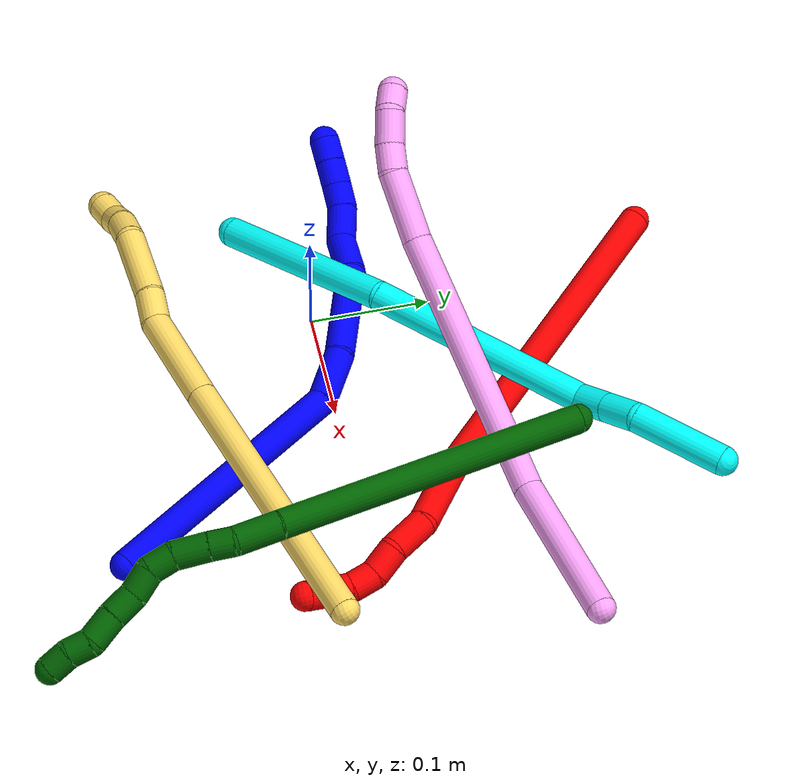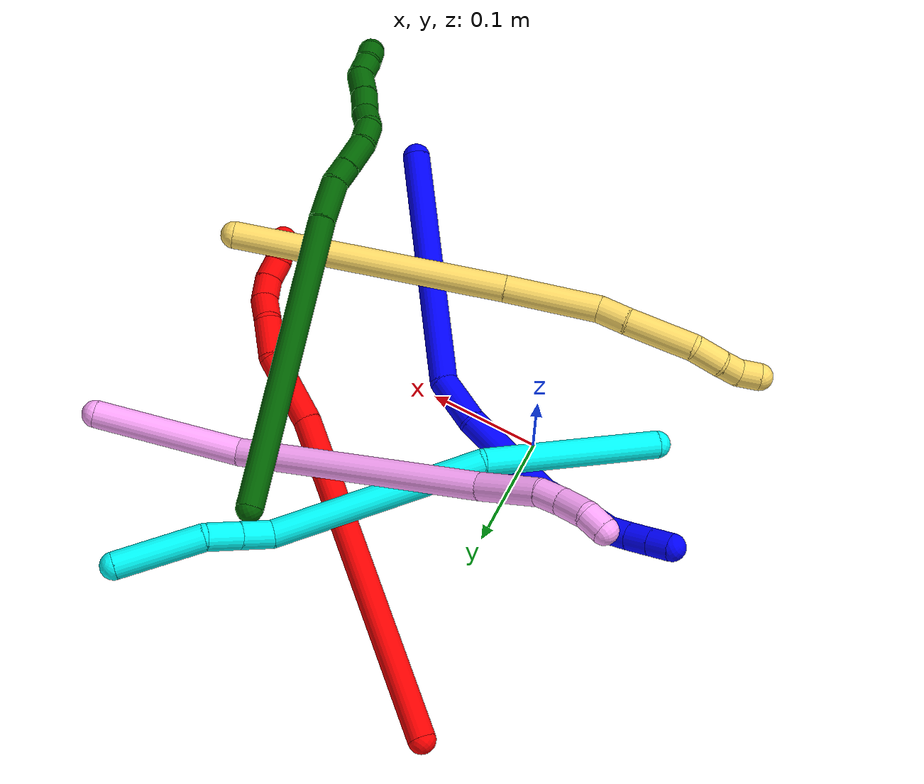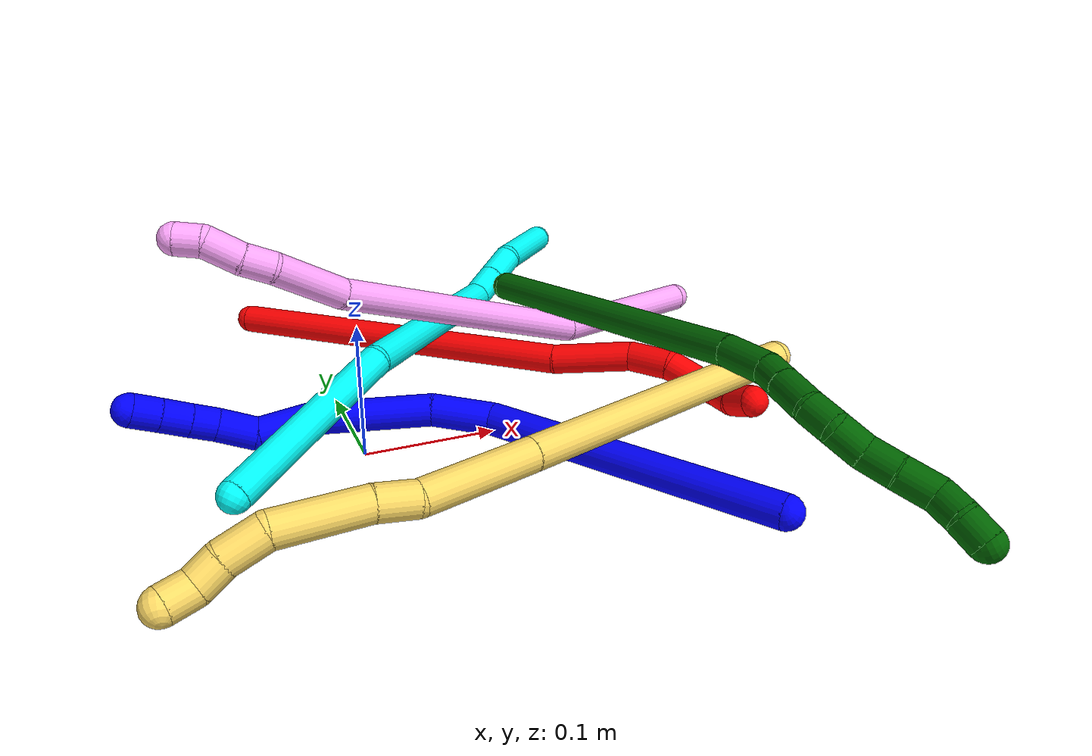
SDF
<sdf version="1.7">
 <world name="default">
  <plugin name="TubeGeneratorPlugin" filename="libtube_generator_plugin.so"/>
  <model name="photoneo_s_sensor">
   <static>1</static>
   <pose>0 0 2 1.57079 1.57079 3.14159</pose>
   <link name="link">
    <inertial><mass>0.1</mass></inertial>
    <sensor name="sensor" type="depth">
     <update_rate>30</update_rate>
     <camera>
      <horizontal_fov>1.22</horizontal_fov>
      <image><width>1920</width><height>1200</height><format>B8G8R8</format></image>
      <clip><near>0.1</near><far>4</far></clip>
      <depth_camera><output>points</output></depth_camera>
     </camera>
     <plugin name="camera_plugin" filename="libgazebo_ros_depth_camera.so">
      <baseline>0.2</baseline>
      <alwaysOn>1</alwaysOn>
      <updateRate>0.0</updateRate>
      <cameraName>camera_ir</cameraName>
      <imageTopicName>/camera/color/image_raw</imageTopicName>
      <cameraInfoTopicName>/camera/color/camera_info</cameraInfoTopicName>
      <depthImageTopicName>/camera/depth/image_raw</depthImageTopicName>
      <depthImageCameraInfoTopicName>/camera/depth/camera_info</depthImageCameraInfoTopicName>
      <pointCloudTopicName>/camera/depth/points</pointCloudTopicName>
      <frameName>fr_optical</frameName>
      <pointCloudCutoff>0.1</pointCloudCutoff>
      <pointCloudCutoffMax>2.0</pointCloudCutoffMax>
      <distortionK1>0</distortionK1>
      <distortionK2>0</distortionK2>
      <distortionK3>0</distortionK3>
      <distortionT1>0</distortionT1>
      <distortionT2>0</distortionT2>
      <CxPrime>0</CxPrime>
      <Cx>0</Cx>
      <Cy>0</Cy>
      <focalLength>0</focalLength>
      <hackBaseline>0</hackBaseline>
     </plugin>
    </sensor>
   </link>
  </model>
  <gravity>0 0 -9.8</gravity>
  <magnetic_field>6e-06 2.3e-05 -4.2e-05</magnetic_field>
  <atmosphere type="adiabatic"/>
  <physics name="default_physics" default="0" type="ode">
   <max_step_size>0.003</max_step_size>
   <real_time_factor>1</real_time_factor>
   <real_time_update_rate>1000</real_time_update_rate>
   <max_contacts>10000</max_contacts>
   <ode>
    <solver>
     <type>quick</type>
     <iters>100</iters>
     <sor>1.3</sor>
     <use_dynamic_moi_rescaling>0</use_dynamic_moi_rescaling>
    </solver>
    <constraints>
     <contact_max_correcting_vel>0</contact_max_correcting_vel>
     <contact_surface_layer>0.001</contact_surface_layer>
     <cfm>0</cfm>
     <erp>0.2</erp>
    </constraints>
   </ode>
  </physics>
  <scene><ambient>0.4 0.4 0.4 1</ambient><background>0.7 0.7 0.7 1</background><shadows>0</shadows></scene>
  <audio><device>default</device></audio>
  <spherical_coordinates>
   <surface_model>EARTH_WGS84</surface_model>
   <latitude_deg>0</latitude_deg>
   <longitude_deg>0</longitude_deg>
   <elevation>0</elevation>
   <heading_deg>0</heading_deg>
  </spherical_coordinates>
  <model name="bin">
   <static>1</static>
   <link name="bottom">
    <collision name="collision-bottom">
     <pose>0 0 -0.01 0 -0 0</pose>
     <geometry><box><size>0.8 0.6 0.02</size></box></geometry>
     <surface>
      <friction><ode><mu>100</mu><mu2>100</mu2></ode></friction>
      <contact><collide_bitmask>65535</collide_bitmask></contact>
     </surface>
    </collision>
   </link>
   <link name="west_wall">
    <collision name="collision-west_wall">
     <pose>-0.41 0 0.1 0 -0 0</pose>
     <geometry><box><size>0.02 0.6 0.2</size></box></geometry>
     <surface>
      <friction><ode><mu>100</mu><mu2>100</mu2></ode></friction>
      <contact><collide_bitmask>65535</collide_bitmask></contact>
     </surface>
    </collision>
   </link>
   <link name="east_wall">
    <collision name="collision-east_wall">
     <pose>0.41 0 0.1 0 -0 0</pose>
     <geometry><box><size>0.02 0.6 0.2</size></box></geometry>
     <surface>
      <friction><ode><mu>100</mu><mu2>100</mu2></ode></friction>
      <contact><collide_bitmask>65535</collide_bitmask></contact>
     </surface>
    </collision>
   </link>
   <link name="south_wall">
    <collision name="collision-south_wall">
     <pose>0 -0.31 0.1 0 -0 0</pose>
     <geometry><box><size>0.8 0.02 0.2</size></box></geometry>
     <surface>
      <friction><ode><mu>100</mu><mu2>100</mu2></ode></friction>
      <contact><collide_bitmask>65535</collide_bitmask></contact>
     </surface>
    </collision>
   </link>
   <link name="north_wall">
    <collision name="collision-north_wall">
     <pose>0 0.31 0.1 0 -0 0</pose>
     <geometry><box><size>0.8 0.02 0.2</size></box></geometry>
     <surface>
      <friction><ode><mu>100</mu><mu2>100</mu2></ode></friction>
      <contact><collide_bitmask>65535</collide_bitmask></contact>
     </surface>
    </collision>
   </link>
  </model>
  <model name="1">
   <static>0</static>
   <link name="1">
    <collision name="collision-cylinder-e_1_1_4">
     <pose>-0.073846 0.087423 -0.008017 -1.66225 -0.699344 0.760372</pose>
     <geometry><cylinder><radius>0.0125</radius><length>0.229437</length></cylinder></geometry>
     <surface>
      <friction><ode><mu>1.16</mu><mu2>1.16</mu2><slip1>0</slip1><slip2>0</slip2></ode></friction>
      <contact><ode><kp>1e+06</kp><kd>1</kd><max_vel>0</max_vel><min_depth>0.001</min_depth></ode></contact>
     </surface>
    </collision>
    <visual name="visual-cylinder-e_1_1_4">
     <pose>-0.073846 0.087423 -0.008017 -1.66225 -0.699344 0.760372</pose>
     <geometry><cylinder><radius>0.0125</radius><length>0.229437</length></cylinder></geometry>
     <material><ambient>0 0 1 1</ambient></material>
    </visual>
    <collision name="collision-cylinder-e_2_4_5">
     <pose>-0.165057 0.188355 -0.008152 -1.04257 -0.837615 0.500545</pose>
     <geometry><cylinder><radius>0.0125</radius><length>0.04674</length></cylinder></geometry>
     <surface>
      <friction><ode><mu>1.16</mu><mu2>1.16</mu2><slip1>0</slip1><slip2>0</slip2></ode></friction>
      <contact><ode><kp>1e+06</kp><kd>1</kd><max_vel>0</max_vel><min_depth>0.001</min_depth></ode></contact>
     </surface>
    </collision>
    <visual name="visual-cylinder-e_2_4_5">
     <pose>-0.165057 0.188355 -0.008152 -1.04257 -0.837615 0.500545</pose>
     <geometry><cylinder><radius>0.0125</radius><length>0.04674</length></cylinder></geometry>
     <material><ambient>0 0 1 1</ambient></material>
    </visual>
    <collision name="collision-cylinder-e_3_5_6">
     <pose>-0.221319 0.218179 0.017955 -0.730198 -1.00941 0.416203</pose>
     <geometry><cylinder><radius>0.0125</radius><length>0.091897</length></cylinder></geometry>
     <surface>
      <friction><ode><mu>1.16</mu><mu2>1.16</mu2><slip1>0</slip1><slip2>0</slip2></ode></friction>
      <contact><ode><kp>1e+06</kp><kd>1</kd><max_vel>0</max_vel><min_depth>0.001</min_depth></ode></contact>
     </surface>
    </collision>
    <visual name="visual-cylinder-e_3_5_6">
     <pose>-0.221319 0.218179 0.017955 -0.730198 -1.00941 0.416203</pose>
     <geometry><cylinder><radius>0.0125</radius><length>0.091897</length></cylinder></geometry>
     <material><ambient>0 0 1 1</ambient></material>
    </visual>
    <collision name="collision-cylinder-e_4_6_7">
     <pose>-0.276978 0.235635 0.046777 -0.107215 -1.00443 0.05892</pose>
     <geometry><cylinder><radius>0.0125</radius><length>0.039729</length></cylinder></geometry>
     <surface>
      <friction><ode><mu>1.16</mu><mu2>1.16</mu2><slip1>0</slip1><slip2>0</slip2></ode></friction>
      <contact><ode><kp>1e+06</kp><kd>1</kd><max_vel>0</max_vel><min_depth>0.001</min_depth></ode></contact>
     </surface>
    </collision>
    <visual name="visual-cylinder-e_4_6_7">
     <pose>-0.276978 0.235635 0.046777 -0.107215 -1.00443 0.05892</pose>
     <geometry><cylinder><radius>0.0125</radius><length>0.039729</length></cylinder></geometry>
     <material><ambient>0 0 1 1</ambient></material>
    </visual>
    <collision name="collision-cylinder-e_5_7_8">
     <pose>-0.302628 0.244153 0.067044 -0.651737 -0.631072 0.219731</pose>
     <geometry><cylinder><radius>0.0125</radius><length>0.030127</length></cylinder></geometry>
     <surface>
      <friction><ode><mu>1.16</mu><mu2>1.16</mu2><slip1>0</slip1><slip2>0</slip2></ode></friction>
      <contact><ode><kp>1e+06</kp><kd>1</kd><max_vel>0</max_vel><min_depth>0.001</min_depth></ode></contact>
     </surface>
    </collision>
    <visual name="visual-cylinder-e_5_7_8">
     <pose>-0.302628 0.244153 0.067044 -0.651737 -0.631072 0.219731</pose>
     <geometry><cylinder><radius>0.0125</radius><length>0.030127</length></cylinder></geometry>
     <material><ambient>0 0 1 1</ambient></material>
    </visual>
    <collision name="collision-cylinder-e_6_8_9">
     <pose>-0.316556 0.254578 0.084862 -0.357841 -0.525093 0.097133</pose>
     <geometry><cylinder><radius>0.0125</radius><length>0.020109</length></cylinder></geometry>
     <surface>
      <friction><ode><mu>1.16</mu><mu2>1.16</mu2><slip1>0</slip1><slip2>0</slip2></ode></friction>
      <contact><ode><kp>1e+06</kp><kd>1</kd><max_vel>0</max_vel><min_depth>0.001</min_depth></ode></contact>
     </surface>
    </collision>
    <visual name="visual-cylinder-e_6_8_9">
     <pose>-0.316556 0.254578 0.084862 -0.357841 -0.525093 0.097133</pose>
     <geometry><cylinder><radius>0.0125</radius><length>0.020109</length></cylinder></geometry>
     <material><ambient>0 0 1 1</ambient></material>
    </visual>
    <collision name="collision-cylinder-e_7_9_10">
     <pose>-0.326709 0.260801 0.10197 -0.340743 -0.493489 0.086611</pose>
     <geometry><cylinder><radius>0.0125</radius><length>0.021585</length></cylinder></geometry>
     <surface>
      <friction><ode><mu>1.16</mu><mu2>1.16</mu2><slip1>0</slip1><slip2>0</slip2></ode></friction>
      <contact><ode><kp>1e+06</kp><kd>1</kd><max_vel>0</max_vel><min_depth>0.001</min_depth></ode></contact>
     </surface>
    </collision>
    <visual name="visual-cylinder-e_7_9_10">
     <pose>-0.326709 0.260801 0.10197 -0.340743 -0.493489 0.086611</pose>
     <geometry><cylinder><radius>0.0125</radius><length>0.021585</length></cylinder></geometry>
     <material><ambient>0 0 1 1</ambient></material>
    </visual>
    <collision name="collision-cylinder-e_8_10_2">
     <pose>-0.336734 0.266894 0.119364 -0.33282 -0.503158 0.086288</pose>
     <geometry><cylinder><radius>0.0125</radius><length>0.020375</length></cylinder></geometry>
     <surface>
      <friction><ode><mu>1.16</mu><mu2>1.16</mu2><slip1>0</slip1><slip2>0</slip2></ode></friction>
      <contact><ode><kp>1e+06</kp><kd>1</kd><max_vel>0</max_vel><min_depth>0.001</min_depth></ode></contact>
     </surface>
    </collision>
    <visual name="visual-cylinder-e_8_10_2">
     <pose>-0.336734 0.266894 0.119364 -0.33282 -0.503158 0.086288</pose>
     <geometry><cylinder><radius>0.0125</radius><length>0.020375</length></cylinder></geometry>
     <material><ambient>0 0 1 1</ambient></material>
    </visual>
    <collision name="collision-sphere-2">
     <pose>-0.341646 0.26981 0.127799 0 -0 0</pose>
     <geometry><sphere><radius>0.0125</radius></sphere></geometry>
     <surface>
      <friction><ode><mu>1.16</mu><mu2>1.16</mu2><slip1>0</slip1><slip2>0</slip2></ode></friction>
      <contact><ode><kp>1e+06</kp><kd>1</kd><max_vel>0</max_vel><min_depth>0.001</min_depth></ode></contact>
     </surface>
    </collision>
    <visual name="visual-sphere-2">
     <pose>-0.341646 0.26981 0.127799 0 -0 0</pose>
     <geometry><sphere><radius>0.0125</radius></sphere></geometry>
     <material><ambient>0 0 1 1</ambient></material>
    </visual>
    <collision name="collision-sphere-10">
     <pose>-0.331821 0.263978 0.110928 0 -0 0</pose>
     <geometry><sphere><radius>0.0125</radius></sphere></geometry>
     <surface>
      <friction><ode><mu>1.16</mu><mu2>1.16</mu2><slip1>0</slip1><slip2>0</slip2></ode></friction>
      <contact><ode><kp>1e+06</kp><kd>1</kd><max_vel>0</max_vel><min_depth>0.001</min_depth></ode></contact>
     </surface>
    </collision>
    <visual name="visual-sphere-10">
     <pose>-0.331821 0.263978 0.110928 0 -0 0</pose>
     <geometry><sphere><radius>0.0125</radius></sphere></geometry>
     <material><ambient>0 0 1 1</ambient></material>
    </visual>
    <collision name="collision-sphere-9">
     <pose>-0.321596 0.257625 0.093011 0 -0 0</pose>
     <geometry><sphere><radius>0.0125</radius></sphere></geometry>
     <surface>
      <friction><ode><mu>1.16</mu><mu2>1.16</mu2><slip1>0</slip1><slip2>0</slip2></ode></friction>
      <contact><ode><kp>1e+06</kp><kd>1</kd><max_vel>0</max_vel><min_depth>0.001</min_depth></ode></contact>
     </surface>
    </collision>
    <visual name="visual-sphere-9">
     <pose>-0.321596 0.257625 0.093011 0 -0 0</pose>
     <geometry><sphere><radius>0.0125</radius></sphere></geometry>
     <material><ambient>0 0 1 1</ambient></material>
    </visual>
    <collision name="collision-sphere-4">
     <pose>-0.147692 0.174846 -0.016035 0 -0 0</pose>
     <geometry><sphere><radius>0.0125</radius></sphere></geometry>
     <surface>
      <friction><ode><mu>1.16</mu><mu2>1.16</mu2><slip1>0</slip1><slip2>0</slip2></ode></friction>
      <contact><ode><kp>1e+06</kp><kd>1</kd><max_vel>0</max_vel><min_depth>0.001</min_depth></ode></contact>
     </surface>
    </collision>
    <visual name="visual-sphere-4">
     <pose>-0.147692 0.174846 -0.016035 0 -0 0</pose>
     <geometry><sphere><radius>0.0125</radius></sphere></geometry>
     <material><ambient>0 0 1 1</ambient></material>
    </visual>
    <collision name="collision-sphere-1">
     <geometry><sphere><radius>0.0125</radius></sphere></geometry>
     <surface>
      <friction><ode><mu>1.16</mu><mu2>1.16</mu2><slip1>0</slip1><slip2>0</slip2></ode></friction>
      <contact><ode><kp>1e+06</kp><kd>1</kd><max_vel>0</max_vel><min_depth>0.001</min_depth></ode></contact>
     </surface>
    </collision>
    <visual name="visual-sphere-1">
     <geometry><sphere><radius>0.0125</radius></sphere></geometry>
     <material><ambient>0 0 1 1</ambient></material>
    </visual>
    <collision name="collision-sphere-8">
     <pose>-0.311516 0.25153 0.076713 0 -0 0</pose>
     <geometry><sphere><radius>0.0125</radius></sphere></geometry>
     <surface>
      <friction><ode><mu>1.16</mu><mu2>1.16</mu2><slip1>0</slip1><slip2>0</slip2></ode></friction>
      <contact><ode><kp>1e+06</kp><kd>1</kd><max_vel>0</max_vel><min_depth>0.001</min_depth></ode></contact>
     </surface>
    </collision>
    <visual name="visual-sphere-8">
     <pose>-0.311516 0.25153 0.076713 0 -0 0</pose>
     <geometry><sphere><radius>0.0125</radius></sphere></geometry>
     <material><ambient>0 0 1 1</ambient></material>
    </visual>
    <collision name="collision-sphere-5">
     <pose>-0.182422 0.201863 -0.000269 0 -0 0</pose>
     <geometry><sphere><radius>0.0125</radius></sphere></geometry>
     <surface>
      <friction><ode><mu>1.16</mu><mu2>1.16</mu2><slip1>0</slip1><slip2>0</slip2></ode></friction>
      <contact><ode><kp>1e+06</kp><kd>1</kd><max_vel>0</max_vel><min_depth>0.001</min_depth></ode></contact>
     </surface>
    </collision>
    <visual name="visual-sphere-5">
     <pose>-0.182422 0.201863 -0.000269 0 -0 0</pose>
     <geometry><sphere><radius>0.0125</radius></sphere></geometry>
     <material><ambient>0 0 1 1</ambient></material>
    </visual>
    <collision name="collision-sphere-6">
     <pose>-0.260215 0.234495 0.03618 0 -0 0</pose>
     <geometry><sphere><radius>0.0125</radius></sphere></geometry>
     <surface>
      <friction><ode><mu>1.16</mu><mu2>1.16</mu2><slip1>0</slip1><slip2>0</slip2></ode></friction>
      <contact><ode><kp>1e+06</kp><kd>1</kd><max_vel>0</max_vel><min_depth>0.001</min_depth></ode></contact>
     </surface>
    </collision>
    <visual name="visual-sphere-6">
     <pose>-0.260215 0.234495 0.03618 0 -0 0</pose>
     <geometry><sphere><radius>0.0125</radius></sphere></geometry>
     <material><ambient>0 0 1 1</ambient></material>
    </visual>
    <collision name="collision-sphere-7">
     <pose>-0.29374 0.236776 0.057375 0 -0 0</pose>
     <geometry><sphere><radius>0.0125</radius></sphere></geometry>
     <surface>
      <friction><ode><mu>1.16</mu><mu2>1.16</mu2><slip1>0</slip1><slip2>0</slip2></ode></friction>
      <contact><ode><kp>1e+06</kp><kd>1</kd><max_vel>0</max_vel><min_depth>0.001</min_depth></ode></contact>
     </surface>
    </collision>
    <visual name="visual-sphere-7">
     <pose>-0.29374 0.236776 0.057375 0 -0 0</pose>
     <geometry><sphere><radius>0.0125</radius></sphere></geometry>
     <material><ambient>0 0 1 1</ambient></material>
    </visual>
    <inertial>
     <pose>-0.170793 0.163632 0.019295 0 -0 0</pose>
     <mass>0.5</mass>
     <inertia>
      <ixx>0.001141</ixx>
      <ixy>0</ixy>
      <ixz>0</ixz>
      <iyy>0.001041</iyy>
      <iyz>0</iyz>
      <izz>-6.8e-05</izz>
     </inertia>
    </inertial>
   </link>
   <pose>0.225927 -0.199859 0.011495 0.747703 -0.604911 -0.320712</pose>
  </model>
  <model name="2">
   <static>0</static>
   <link name="2">
    <collision name="collision-cylinder-e_1_1_4">
     <pose>0.050099 -0.108665 0.09773 0.83833 0.330243 0.148227</pose>
     <geometry><cylinder><radius>0.0125</radius><length>0.308992</length></cylinder></geometry>
     <surface>
      <friction><ode><mu>1.16</mu><mu2>1.16</mu2><slip1>0</slip1><slip2>0</slip2></ode></friction>
      <contact><ode><kp>1e+06</kp><kd>1</kd><max_vel>0</max_vel><min_depth>0.001</min_depth></ode></contact>
     </surface>
    </collision>
    <visual name="visual-cylinder-e_1_1_4">
     <pose>0.050099 -0.108665 0.09773 0.83833 0.330243 0.148227</pose>
     <geometry><cylinder><radius>0.0125</radius><length>0.308992</length></cylinder></geometry>
     <material><ambient>1 0 0 1</ambient></material>
    </visual>
    <collision name="collision-cylinder-e_2_4_5">
     <pose>0.115015 -0.242303 0.211619 0.996471 0.462157 0.254608</pose>
     <geometry><cylinder><radius>0.0125</radius><length>0.066466</length></cylinder></geometry>
     <surface>
      <friction><ode><mu>1.16</mu><mu2>1.16</mu2><slip1>0</slip1><slip2>0</slip2></ode></friction>
      <contact><ode><kp>1e+06</kp><kd>1</kd><max_vel>0</max_vel><min_depth>0.001</min_depth></ode></contact>
     </surface>
    </collision>
    <visual name="visual-cylinder-e_2_4_5">
     <pose>0.115015 -0.242303 0.211619 0.996471 0.462157 0.254608</pose>
     <geometry><cylinder><radius>0.0125</radius><length>0.066466</length></cylinder></geometry>
     <material><ambient>1 0 0 1</ambient></material>
    </visual>
    <collision name="collision-cylinder-e_3_5_6">
     <pose>0.134797 -0.277608 0.241687 0.638916 0.279012 0.09283</pose>
     <geometry><cylinder><radius>0.0125</radius><length>0.036045</length></cylinder></geometry>
     <surface>
      <friction><ode><mu>1.16</mu><mu2>1.16</mu2><slip1>0</slip1><slip2>0</slip2></ode></friction>
      <contact><ode><kp>1e+06</kp><kd>1</kd><max_vel>0</max_vel><min_depth>0.001</min_depth></ode></contact>
     </surface>
    </collision>
    <visual name="visual-cylinder-e_3_5_6">
     <pose>0.134797 -0.277608 0.241687 0.638916 0.279012 0.09283</pose>
     <geometry><cylinder><radius>0.0125</radius><length>0.036045</length></cylinder></geometry>
     <material><ambient>1 0 0 1</ambient></material>
    </visual>
    <collision name="collision-cylinder-e_4_6_7">
     <pose>0.139034 -0.296572 0.265203 0.731991 -0.056193 -0.021542</pose>
     <geometry><cylinder><radius>0.0125</radius><length>0.025873</length></cylinder></geometry>
     <surface>
      <friction><ode><mu>1.16</mu><mu2>1.16</mu2><slip1>0</slip1><slip2>0</slip2></ode></friction>
      <contact><ode><kp>1e+06</kp><kd>1</kd><max_vel>0</max_vel><min_depth>0.001</min_depth></ode></contact>
     </surface>
    </collision>
    <visual name="visual-cylinder-e_4_6_7">
     <pose>0.139034 -0.296572 0.265203 0.731991 -0.056193 -0.021542</pose>
     <geometry><cylinder><radius>0.0125</radius><length>0.025873</length></cylinder></geometry>
     <material><ambient>1 0 0 1</ambient></material>
    </visual>
    <collision name="collision-cylinder-e_5_7_8">
     <pose>0.139715 -0.30933 0.285144 0.379799 0.125849 0.024221</pose>
     <geometry><cylinder><radius>0.0125</radius><length>0.022431</length></cylinder></geometry>
     <surface>
      <friction><ode><mu>1.16</mu><mu2>1.16</mu2><slip1>0</slip1><slip2>0</slip2></ode></friction>
      <contact><ode><kp>1e+06</kp><kd>1</kd><max_vel>0</max_vel><min_depth>0.001</min_depth></ode></contact>
     </surface>
    </collision>
    <visual name="visual-cylinder-e_5_7_8">
     <pose>0.139715 -0.30933 0.285144 0.379799 0.125849 0.024221</pose>
     <geometry><cylinder><radius>0.0125</radius><length>0.022431</length></cylinder></geometry>
     <material><ambient>1 0 0 1</ambient></material>
    </visual>
    <collision name="collision-cylinder-e_6_8_9">
     <pose>0.142758 -0.313933 0.305349 0.048404 0.163969 0.003978</pose>
     <geometry><cylinder><radius>0.0125</radius><length>0.020034</length></cylinder></geometry>
     <surface>
      <friction><ode><mu>1.16</mu><mu2>1.16</mu2><slip1>0</slip1><slip2>0</slip2></ode></friction>
      <contact><ode><kp>1e+06</kp><kd>1</kd><max_vel>0</max_vel><min_depth>0.001</min_depth></ode></contact>
     </surface>
    </collision>
    <visual name="visual-cylinder-e_6_8_9">
     <pose>0.142758 -0.313933 0.305349 0.048404 0.163969 0.003978</pose>
     <geometry><cylinder><radius>0.0125</radius><length>0.020034</length></cylinder></geometry>
     <material><ambient>1 0 0 1</ambient></material>
    </visual>
    <collision name="collision-cylinder-e_7_9_2">
     <pose>0.149327 -0.315668 0.32392 0.143427 0.511497 0.037563</pose>
     <geometry><cylinder><radius>0.0125</radius><length>0.02016</length></cylinder></geometry>
     <surface>
      <friction><ode><mu>1.16</mu><mu2>1.16</mu2><slip1>0</slip1><slip2>0</slip2></ode></friction>
      <contact><ode><kp>1e+06</kp><kd>1</kd><max_vel>0</max_vel><min_depth>0.001</min_depth></ode></contact>
     </surface>
    </collision>
    <visual name="visual-cylinder-e_7_9_2">
     <pose>0.149327 -0.315668 0.32392 0.143427 0.511497 0.037563</pose>
     <geometry><cylinder><radius>0.0125</radius><length>0.02016</length></cylinder></geometry>
     <material><ambient>1 0 0 1</ambient></material>
    </visual>
    <collision name="collision-sphere-2">
     <pose>0.154261 -0.316924 0.33262 0 -0 0</pose>
     <geometry><sphere><radius>0.0125</radius></sphere></geometry>
     <surface>
      <friction><ode><mu>1.16</mu><mu2>1.16</mu2><slip1>0</slip1><slip2>0</slip2></ode></friction>
      <contact><ode><kp>1e+06</kp><kd>1</kd><max_vel>0</max_vel><min_depth>0.001</min_depth></ode></contact>
     </surface>
    </collision>
    <visual name="visual-sphere-2">
     <pose>0.154261 -0.316924 0.33262 0 -0 0</pose>
     <geometry><sphere><radius>0.0125</radius></sphere></geometry>
     <material><ambient>1 0 0 1</ambient></material>
    </visual>
    <collision name="collision-sphere-9">
     <pose>0.144393 -0.314411 0.31522 0 -0 0</pose>
     <geometry><sphere><radius>0.0125</radius></sphere></geometry>
     <surface>
      <friction><ode><mu>1.16</mu><mu2>1.16</mu2><slip1>0</slip1><slip2>0</slip2></ode></friction>
      <contact><ode><kp>1e+06</kp><kd>1</kd><max_vel>0</max_vel><min_depth>0.001</min_depth></ode></contact>
     </surface>
    </collision>
    <visual name="visual-sphere-9">
     <pose>0.144393 -0.314411 0.31522 0 -0 0</pose>
     <geometry><sphere><radius>0.0125</radius></sphere></geometry>
     <material><ambient>1 0 0 1</ambient></material>
    </visual>
    <collision name="collision-sphere-4">
     <pose>0.100198 -0.217329 0.195459 0 -0 0</pose>
     <geometry><sphere><radius>0.0125</radius></sphere></geometry>
     <surface>
      <friction><ode><mu>1.16</mu><mu2>1.16</mu2><slip1>0</slip1><slip2>0</slip2></ode></friction>
      <contact><ode><kp>1e+06</kp><kd>1</kd><max_vel>0</max_vel><min_depth>0.001</min_depth></ode></contact>
     </surface>
    </collision>
    <visual name="visual-sphere-4">
     <pose>0.100198 -0.217329 0.195459 0 -0 0</pose>
     <geometry><sphere><radius>0.0125</radius></sphere></geometry>
     <material><ambient>1 0 0 1</ambient></material>
    </visual>
    <collision name="collision-sphere-1">
     <geometry><sphere><radius>0.0125</radius></sphere></geometry>
     <surface>
      <friction><ode><mu>1.16</mu><mu2>1.16</mu2><slip1>0</slip1><slip2>0</slip2></ode></friction>
      <contact><ode><kp>1e+06</kp><kd>1</kd><max_vel>0</max_vel><min_depth>0.001</min_depth></ode></contact>
     </surface>
    </collision>
    <visual name="visual-sphere-1">
     <geometry><sphere><radius>0.0125</radius></sphere></geometry>
     <material><ambient>1 0 0 1</ambient></material>
    </visual>
    <collision name="collision-sphere-8">
     <pose>0.141123 -0.313455 0.295478 0 -0 0</pose>
     <geometry><sphere><radius>0.0125</radius></sphere></geometry>
     <surface>
      <friction><ode><mu>1.16</mu><mu2>1.16</mu2><slip1>0</slip1><slip2>0</slip2></ode></friction>
      <contact><ode><kp>1e+06</kp><kd>1</kd><max_vel>0</max_vel><min_depth>0.001</min_depth></ode></contact>
     </surface>
    </collision>
    <visual name="visual-sphere-8">
     <pose>0.141123 -0.313455 0.295478 0 -0 0</pose>
     <geometry><sphere><radius>0.0125</radius></sphere></geometry>
     <material><ambient>1 0 0 1</ambient></material>
    </visual>
    <collision name="collision-sphere-5">
     <pose>0.129833 -0.267277 0.22778 0 -0 0</pose>
     <geometry><sphere><radius>0.0125</radius></sphere></geometry>
     <surface>
      <friction><ode><mu>1.16</mu><mu2>1.16</mu2><slip1>0</slip1><slip2>0</slip2></ode></friction>
      <contact><ode><kp>1e+06</kp><kd>1</kd><max_vel>0</max_vel><min_depth>0.001</min_depth></ode></contact>
     </surface>
    </collision>
    <visual name="visual-sphere-5">
     <pose>0.129833 -0.267277 0.22778 0 -0 0</pose>
     <geometry><sphere><radius>0.0125</radius></sphere></geometry>
     <material><ambient>1 0 0 1</ambient></material>
    </visual>
    <collision name="collision-sphere-6">
     <pose>0.13976 -0.28794 0.255595 0 -0 0</pose>
     <geometry><sphere><radius>0.0125</radius></sphere></geometry>
     <surface>
      <friction><ode><mu>1.16</mu><mu2>1.16</mu2><slip1>0</slip1><slip2>0</slip2></ode></friction>
      <contact><ode><kp>1e+06</kp><kd>1</kd><max_vel>0</max_vel><min_depth>0.001</min_depth></ode></contact>
     </surface>
    </collision>
    <visual name="visual-sphere-6">
     <pose>0.13976 -0.28794 0.255595 0 -0 0</pose>
     <geometry><sphere><radius>0.0125</radius></sphere></geometry>
     <material><ambient>1 0 0 1</ambient></material>
    </visual>
    <collision name="collision-sphere-7">
     <pose>0.138307 -0.305205 0.27481 0 -0 0</pose>
     <geometry><sphere><radius>0.0125</radius></sphere></geometry>
     <surface>
      <friction><ode><mu>1.16</mu><mu2>1.16</mu2><slip1>0</slip1><slip2>0</slip2></ode></friction>
      <contact><ode><kp>1e+06</kp><kd>1</kd><max_vel>0</max_vel><min_depth>0.001</min_depth></ode></contact>
     </surface>
    </collision>
    <visual name="visual-sphere-7">
     <pose>0.138307 -0.305205 0.27481 0 -0 0</pose>
     <geometry><sphere><radius>0.0125</radius></sphere></geometry>
     <material><ambient>1 0 0 1</ambient></material>
    </visual>
    <inertial>
     <pose>0.08117 -0.173905 0.15776 0 -0 0</pose>
     <mass>0.5</mass>
     <inertia>
      <ixx>0.002711</ixx>
      <ixy>0</ixy>
      <ixz>0</ixz>
      <iyy>0.002076</iyy>
      <iyz>0</iyz>
      <izz>0.000974</izz>
     </inertia>
    </inertial>
   </link>
   <pose>-0.040381 0.288507 0.012498 1.88017 -1.21997 -0.34345</pose>
  </model>
  <model name="3">
   <static>0</static>
   <link name="3">
    <collision name="collision-cylinder-e_1_1_4">
     <pose>0.03558 0.028752 0.06717 -0.404447 0.45316 -0.094463</pose>
     <geometry><cylinder><radius>0.0125</radius><length>0.162534</length></cylinder></geometry>
     <surface>
      <friction><ode><mu>1.16</mu><mu2>1.16</mu2><slip1>0</slip1><slip2>0</slip2></ode></friction>
      <contact><ode><kp>1e+06</kp><kd>1</kd><max_vel>0</max_vel><min_depth>0.001</min_depth></ode></contact>
     </surface>
    </collision>
    <visual name="visual-cylinder-e_1_1_4">
     <pose>0.03558 0.028752 0.06717 -0.404447 0.45316 -0.094463</pose>
     <geometry><cylinder><radius>0.0125</radius><length>0.162534</length></cylinder></geometry>
     <material><ambient>0.003922 1 0.996078 1</ambient></material>
    </visual>
    <collision name="collision-cylinder-e_2_4_5">
     <pose>0.126665 0.110489 0.194239 -0.724229 0.606736 -0.236061</pose>
     <geometry><cylinder><radius>0.0125</radius><length>0.194692</length></cylinder></geometry>
     <surface>
      <friction><ode><mu>1.16</mu><mu2>1.16</mu2><slip1>0</slip1><slip2>0</slip2></ode></friction>
      <contact><ode><kp>1e+06</kp><kd>1</kd><max_vel>0</max_vel><min_depth>0.001</min_depth></ode></contact>
     </surface>
    </collision>
    <visual name="visual-cylinder-e_2_4_5">
     <pose>0.126665 0.110489 0.194239 -0.724229 0.606736 -0.236061</pose>
     <geometry><cylinder><radius>0.0125</radius><length>0.194692</length></cylinder></geometry>
     <material><ambient>0.003922 1 0.996078 1</ambient></material>
    </visual>
    <collision name="collision-cylinder-e_3_5_6">
     <pose>0.187239 0.167802 0.267531 -0.312522 0.345665 -0.054993</pose>
     <geometry><cylinder><radius>0.0125</radius><length>0.029918</length></cylinder></geometry>
     <surface>
      <friction><ode><mu>1.16</mu><mu2>1.16</mu2><slip1>0</slip1><slip2>0</slip2></ode></friction>
      <contact><ode><kp>1e+06</kp><kd>1</kd><max_vel>0</max_vel><min_depth>0.001</min_depth></ode></contact>
     </surface>
    </collision>
    <visual name="visual-cylinder-e_3_5_6">
     <pose>0.187239 0.167802 0.267531 -0.312522 0.345665 -0.054993</pose>
     <geometry><cylinder><radius>0.0125</radius><length>0.029918</length></cylinder></geometry>
     <material><ambient>0.003922 1 0.996078 1</ambient></material>
    </visual>
    <collision name="collision-cylinder-e_4_6_7">
     <pose>0.19769 0.176781 0.295085 -0.317381 0.346513 -0.056002</pose>
     <geometry><cylinder><radius>0.0125</radius><length>0.031697</length></cylinder></geometry>
     <surface>
      <friction><ode><mu>1.16</mu><mu2>1.16</mu2><slip1>0</slip1><slip2>0</slip2></ode></friction>
      <contact><ode><kp>1e+06</kp><kd>1</kd><max_vel>0</max_vel><min_depth>0.001</min_depth></ode></contact>
     </surface>
    </collision>
    <visual name="visual-cylinder-e_4_6_7">
     <pose>0.19769 0.176781 0.295085 -0.317381 0.346513 -0.056002</pose>
     <geometry><cylinder><radius>0.0125</radius><length>0.031697</length></cylinder></geometry>
     <material><ambient>0.003922 1 0.996078 1</ambient></material>
    </visual>
    <collision name="collision-cylinder-e_5_7_2">
     <pose>0.225721 0.202804 0.335266 -0.687626 0.59214 -0.217563</pose>
     <geometry><cylinder><radius>0.0125</radius><length>0.081158</length></cylinder></geometry>
     <surface>
      <friction><ode><mu>1.16</mu><mu2>1.16</mu2><slip1>0</slip1><slip2>0</slip2></ode></friction>
      <contact><ode><kp>1e+06</kp><kd>1</kd><max_vel>0</max_vel><min_depth>0.001</min_depth></ode></contact>
     </surface>
    </collision>
    <visual name="visual-cylinder-e_5_7_2">
     <pose>0.225721 0.202804 0.335266 -0.687626 0.59214 -0.217563</pose>
     <geometry><cylinder><radius>0.0125</radius><length>0.081158</length></cylinder></geometry>
     <material><ambient>0.003922 1 0.996078 1</ambient></material>
    </visual>
    <collision name="collision-sphere-2">
     <pose>0.24837 0.224175 0.361285 0 -0 0</pose>
     <geometry><sphere><radius>0.0125</radius></sphere></geometry>
     <surface>
      <friction><ode><mu>1.16</mu><mu2>1.16</mu2><slip1>0</slip1><slip2>0</slip2></ode></friction>
      <contact><ode><kp>1e+06</kp><kd>1</kd><max_vel>0</max_vel><min_depth>0.001</min_depth></ode></contact>
     </surface>
    </collision>
    <visual name="visual-sphere-2">
     <pose>0.24837 0.224175 0.361285 0 -0 0</pose>
     <geometry><sphere><radius>0.0125</radius></sphere></geometry>
     <material><ambient>0.003922 1 0.996078 1</ambient></material>
    </visual>
    <collision name="collision-sphere-7">
     <pose>0.203072 0.181433 0.309247 0 -0 0</pose>
     <geometry><sphere><radius>0.0125</radius></sphere></geometry>
     <surface>
      <friction><ode><mu>1.16</mu><mu2>1.16</mu2><slip1>0</slip1><slip2>0</slip2></ode></friction>
      <contact><ode><kp>1e+06</kp><kd>1</kd><max_vel>0</max_vel><min_depth>0.001</min_depth></ode></contact>
     </surface>
    </collision>
    <visual name="visual-sphere-7">
     <pose>0.203072 0.181433 0.309247 0 -0 0</pose>
     <geometry><sphere><radius>0.0125</radius></sphere></geometry>
     <material><ambient>0.003922 1 0.996078 1</ambient></material>
    </visual>
    <collision name="collision-sphere-6">
     <pose>0.192307 0.172129 0.280923 0 -0 0</pose>
     <geometry><sphere><radius>0.0125</radius></sphere></geometry>
     <surface>
      <friction><ode><mu>1.16</mu><mu2>1.16</mu2><slip1>0</slip1><slip2>0</slip2></ode></friction>
      <contact><ode><kp>1e+06</kp><kd>1</kd><max_vel>0</max_vel><min_depth>0.001</min_depth></ode></contact>
     </surface>
    </collision>
    <visual name="visual-sphere-6">
     <pose>0.192307 0.172129 0.280923 0 -0 0</pose>
     <geometry><sphere><radius>0.0125</radius></sphere></geometry>
     <material><ambient>0.003922 1 0.996078 1</ambient></material>
    </visual>
    <collision name="collision-sphere-5">
     <pose>0.18217 0.163475 0.254138 0 -0 0</pose>
     <geometry><sphere><radius>0.0125</radius></sphere></geometry>
     <surface>
      <friction><ode><mu>1.16</mu><mu2>1.16</mu2><slip1>0</slip1><slip2>0</slip2></ode></friction>
      <contact><ode><kp>1e+06</kp><kd>1</kd><max_vel>0</max_vel><min_depth>0.001</min_depth></ode></contact>
     </surface>
    </collision>
    <visual name="visual-sphere-5">
     <pose>0.18217 0.163475 0.254138 0 -0 0</pose>
     <geometry><sphere><radius>0.0125</radius></sphere></geometry>
     <material><ambient>0.003922 1 0.996078 1</ambient></material>
    </visual>
    <collision name="collision-sphere-1">
     <geometry><sphere><radius>0.0125</radius></sphere></geometry>
     <surface>
      <friction><ode><mu>1.16</mu><mu2>1.16</mu2><slip1>0</slip1><slip2>0</slip2></ode></friction>
      <contact><ode><kp>1e+06</kp><kd>1</kd><max_vel>0</max_vel><min_depth>0.001</min_depth></ode></contact>
     </surface>
    </collision>
    <visual name="visual-sphere-1">
     <geometry><sphere><radius>0.0125</radius></sphere></geometry>
     <material><ambient>0.003922 1 0.996078 1</ambient></material>
    </visual>
    <collision name="collision-sphere-4">
     <pose>0.071159 0.057503 0.13434 0 -0 0</pose>
     <geometry><sphere><radius>0.0125</radius></sphere></geometry>
     <surface>
      <friction><ode><mu>1.16</mu><mu2>1.16</mu2><slip1>0</slip1><slip2>0</slip2></ode></friction>
      <contact><ode><kp>1e+06</kp><kd>1</kd><max_vel>0</max_vel><min_depth>0.001</min_depth></ode></contact>
     </surface>
    </collision>
    <visual name="visual-sphere-4">
     <pose>0.071159 0.057503 0.13434 0 -0 0</pose>
     <geometry><sphere><radius>0.0125</radius></sphere></geometry>
     <material><ambient>0.003922 1 0.996078 1</ambient></material>
    </visual>
    <inertial>
     <pose>0.121261 0.106535 0.186602 0 -0 0</pose>
     <mass>0.5</mass>
     <inertia>
      <ixx>0.000729</ixx>
      <ixy>0</ixy>
      <ixz>0</ixz>
      <iyy>0.000752</iyy>
      <iyz>0</iyz>
      <izz>-0.00101</izz>
     </inertia>
    </inertial>
   </link>
   <pose>-0.098213 -0.047335 0.013242 -0.322473 0.702963 0.024151</pose>
  </model>
  <model name="4">
   <static>0</static>
   <link name="4">
    <collision name="collision-cylinder-e_1_1_4">
     <pose>-0.058316 0.021165 -0.025637 -2.45145 -1.05268 2.03353</pose>
     <geometry><cylinder><radius>0.0125</radius><length>0.134254</length></cylinder></geometry>
     <surface>
      <friction><ode><mu>1.16</mu><mu2>1.16</mu2><slip1>0</slip1><slip2>0</slip2></ode></friction>
      <contact><ode><kp>1e+06</kp><kd>1</kd><max_vel>0</max_vel><min_depth>0.001</min_depth></ode></contact>
     </surface>
    </collision>
    <visual name="visual-cylinder-e_1_1_4">
     <pose>-0.058316 0.021165 -0.025637 -2.45145 -1.05268 2.03353</pose>
     <geometry><cylinder><radius>0.0125</radius><length>0.134254</length></cylinder></geometry>
     <material><ambient>1 0.65098 0.996078 1</ambient></material>
    </visual>
    <collision name="collision-cylinder-e_2_4_5">
     <pose>-0.229973 0.044804 -0.07711 -3.0461 -1.34567 3.02181</pose>
     <geometry><cylinder><radius>0.0125</radius><length>0.232547</length></cylinder></geometry>
     <surface>
      <friction><ode><mu>1.16</mu><mu2>1.16</mu2><slip1>0</slip1><slip2>0</slip2></ode></friction>
      <contact><ode><kp>1e+06</kp><kd>1</kd><max_vel>0</max_vel><min_depth>0.001</min_depth></ode></contact>
     </surface>
    </collision>
    <visual name="visual-cylinder-e_2_4_5">
     <pose>-0.229973 0.044804 -0.07711 -3.0461 -1.34567 3.02181</pose>
     <geometry><cylinder><radius>0.0125</radius><length>0.232547</length></cylinder></geometry>
     <material><ambient>1 0.65098 0.996078 1</ambient></material>
    </visual>
    <collision name="collision-cylinder-e_3_5_6">
     <pose>-0.372903 0.043565 -0.106049 2.26667 -1.40871 -2.13533</pose>
     <geometry><cylinder><radius>0.0125</radius><length>0.059968</length></cylinder></geometry>
     <surface>
      <friction><ode><mu>1.16</mu><mu2>1.16</mu2><slip1>0</slip1><slip2>0</slip2></ode></friction>
      <contact><ode><kp>1e+06</kp><kd>1</kd><max_vel>0</max_vel><min_depth>0.001</min_depth></ode></contact>
     </surface>
    </collision>
    <visual name="visual-cylinder-e_3_5_6">
     <pose>-0.372903 0.043565 -0.106049 2.26667 -1.40871 -2.13533</pose>
     <geometry><cylinder><radius>0.0125</radius><length>0.059968</length></cylinder></geometry>
     <material><ambient>1 0.65098 0.996078 1</ambient></material>
    </visual>
    <collision name="collision-cylinder-e_4_6_7">
     <pose>-0.414387 0.040962 -0.108551 -1.07497 -1.46509 0.984248</pose>
     <geometry><cylinder><radius>0.0125</radius><length>0.023919</length></cylinder></geometry>
     <surface>
      <friction><ode><mu>1.16</mu><mu2>1.16</mu2><slip1>0</slip1><slip2>0</slip2></ode></friction>
      <contact><ode><kp>1e+06</kp><kd>1</kd><max_vel>0</max_vel><min_depth>0.001</min_depth></ode></contact>
     </surface>
    </collision>
    <visual name="visual-cylinder-e_4_6_7">
     <pose>-0.414387 0.040962 -0.108551 -1.07497 -1.46509 0.984248</pose>
     <geometry><cylinder><radius>0.0125</radius><length>0.023919</length></cylinder></geometry>
     <material><ambient>1 0.65098 0.996078 1</ambient></material>
    </visual>
    <collision name="collision-cylinder-e_5_7_8">
     <pose>-0.440468 0.042212 -0.104877 -0.045831 -1.35728 0.036961</pose>
     <geometry><cylinder><radius>0.0125</radius><length>0.029036</length></cylinder></geometry>
     <surface>
      <friction><ode><mu>1.16</mu><mu2>1.16</mu2><slip1>0</slip1><slip2>0</slip2></ode></friction>
      <contact><ode><kp>1e+06</kp><kd>1</kd><max_vel>0</max_vel><min_depth>0.001</min_depth></ode></contact>
     </surface>
    </collision>
    <visual name="visual-cylinder-e_5_7_8">
     <pose>-0.440468 0.042212 -0.104877 -0.045831 -1.35728 0.036961</pose>
     <geometry><cylinder><radius>0.0125</radius><length>0.029036</length></cylinder></geometry>
     <material><ambient>1 0.65098 0.996078 1</ambient></material>
    </visual>
    <collision name="collision-cylinder-e_6_8_2">
     <pose>-0.463724 0.046608 -0.100238 -1.21812 -1.10715 0.814033</pose>
     <geometry><cylinder><radius>0.0125</radius><length>0.020277</length></cylinder></geometry>
     <surface>
      <friction><ode><mu>1.16</mu><mu2>1.16</mu2><slip1>0</slip1><slip2>0</slip2></ode></friction>
      <contact><ode><kp>1e+06</kp><kd>1</kd><max_vel>0</max_vel><min_depth>0.001</min_depth></ode></contact>
     </surface>
    </collision>
    <visual name="visual-cylinder-e_6_8_2">
     <pose>-0.463724 0.046608 -0.100238 -1.21812 -1.10715 0.814033</pose>
     <geometry><cylinder><radius>0.0125</radius><length>0.020277</length></cylinder></geometry>
     <material><ambient>1 0.65098 0.996078 1</ambient></material>
    </visual>
    <collision name="collision-sphere-2">
     <pose>-0.472792 0.050863 -0.098672 0 -0 0</pose>
     <geometry><sphere><radius>0.0125</radius></sphere></geometry>
     <surface>
      <friction><ode><mu>1.16</mu><mu2>1.16</mu2><slip1>0</slip1><slip2>0</slip2></ode></friction>
      <contact><ode><kp>1e+06</kp><kd>1</kd><max_vel>0</max_vel><min_depth>0.001</min_depth></ode></contact>
     </surface>
    </collision>
    <visual name="visual-sphere-2">
     <pose>-0.472792 0.050863 -0.098672 0 -0 0</pose>
     <geometry><sphere><radius>0.0125</radius></sphere></geometry>
     <material><ambient>1 0.65098 0.996078 1</ambient></material>
    </visual>
    <collision name="collision-sphere-4">
     <pose>-0.116633 0.04233 -0.051273 0 -0 0</pose>
     <geometry><sphere><radius>0.0125</radius></sphere></geometry>
     <surface>
      <friction><ode><mu>1.16</mu><mu2>1.16</mu2><slip1>0</slip1><slip2>0</slip2></ode></friction>
      <contact><ode><kp>1e+06</kp><kd>1</kd><max_vel>0</max_vel><min_depth>0.001</min_depth></ode></contact>
     </surface>
    </collision>
    <visual name="visual-sphere-4">
     <pose>-0.116633 0.04233 -0.051273 0 -0 0</pose>
     <geometry><sphere><radius>0.0125</radius></sphere></geometry>
     <material><ambient>1 0.65098 0.996078 1</ambient></material>
    </visual>
    <collision name="collision-sphere-1">
     <geometry><sphere><radius>0.0125</radius></sphere></geometry>
     <surface>
      <friction><ode><mu>1.16</mu><mu2>1.16</mu2><slip1>0</slip1><slip2>0</slip2></ode></friction>
      <contact><ode><kp>1e+06</kp><kd>1</kd><max_vel>0</max_vel><min_depth>0.001</min_depth></ode></contact>
     </surface>
    </collision>
    <visual name="visual-sphere-1">
     <geometry><sphere><radius>0.0125</radius></sphere></geometry>
     <material><ambient>1 0.65098 0.996078 1</ambient></material>
    </visual>
    <collision name="collision-sphere-8">
     <pose>-0.454656 0.042353 -0.101804 0 -0 0</pose>
     <geometry><sphere><radius>0.0125</radius></sphere></geometry>
     <surface>
      <friction><ode><mu>1.16</mu><mu2>1.16</mu2><slip1>0</slip1><slip2>0</slip2></ode></friction>
      <contact><ode><kp>1e+06</kp><kd>1</kd><max_vel>0</max_vel><min_depth>0.001</min_depth></ode></contact>
     </surface>
    </collision>
    <visual name="visual-sphere-8">
     <pose>-0.454656 0.042353 -0.101804 0 -0 0</pose>
     <geometry><sphere><radius>0.0125</radius></sphere></geometry>
     <material><ambient>1 0.65098 0.996078 1</ambient></material>
    </visual>
    <collision name="collision-sphere-5">
     <pose>-0.343312 0.047279 -0.102947 0 -0 0</pose>
     <geometry><sphere><radius>0.0125</radius></sphere></geometry>
     <surface>
      <friction><ode><mu>1.16</mu><mu2>1.16</mu2><slip1>0</slip1><slip2>0</slip2></ode></friction>
      <contact><ode><kp>1e+06</kp><kd>1</kd><max_vel>0</max_vel><min_depth>0.001</min_depth></ode></contact>
     </surface>
    </collision>
    <visual name="visual-sphere-5">
     <pose>-0.343312 0.047279 -0.102947 0 -0 0</pose>
     <geometry><sphere><radius>0.0125</radius></sphere></geometry>
     <material><ambient>1 0.65098 0.996078 1</ambient></material>
    </visual>
    <collision name="collision-sphere-6">
     <pose>-0.402494 0.039852 -0.109151 0 -0 0</pose>
     <geometry><sphere><radius>0.0125</radius></sphere></geometry>
     <surface>
      <friction><ode><mu>1.16</mu><mu2>1.16</mu2><slip1>0</slip1><slip2>0</slip2></ode></friction>
      <contact><ode><kp>1e+06</kp><kd>1</kd><max_vel>0</max_vel><min_depth>0.001</min_depth></ode></contact>
     </surface>
    </collision>
    <visual name="visual-sphere-6">
     <pose>-0.402494 0.039852 -0.109151 0 -0 0</pose>
     <geometry><sphere><radius>0.0125</radius></sphere></geometry>
     <material><ambient>1 0.65098 0.996078 1</ambient></material>
    </visual>
    <collision name="collision-sphere-7">
     <pose>-0.426279 0.042072 -0.10795 0 -0 0</pose>
     <geometry><sphere><radius>0.0125</radius></sphere></geometry>
     <surface>
      <friction><ode><mu>1.16</mu><mu2>1.16</mu2><slip1>0</slip1><slip2>0</slip2></ode></friction>
      <contact><ode><kp>1e+06</kp><kd>1</kd><max_vel>0</max_vel><min_depth>0.001</min_depth></ode></contact>
     </surface>
    </collision>
    <visual name="visual-sphere-7">
     <pose>-0.426279 0.042072 -0.10795 0 -0 0</pose>
     <geometry><sphere><radius>0.0125</radius></sphere></geometry>
     <material><ambient>1 0.65098 0.996078 1</ambient></material>
    </visual>
    <inertial>
     <pose>-0.231549 0.038047 -0.070814 0 -0 0</pose>
     <mass>0.5</mass>
     <inertia>
      <ixx>-0.0002</ixx>
      <ixy>0</ixy>
      <ixz>0</ixz>
      <iyy>0.001378</iyy>
      <iyz>0</iyz>
      <izz>0.001143</izz>
     </inertia>
    </inertial>
   </link>
   <pose>0.355338 0.164814 0.022028 -1.13253 0.455709 0.009176</pose>
  </model>
  <model name="5">
   <static>0</static>
   <link name="5">
    <collision name="collision-cylinder-e_1_1_4">
     <pose>-0.11909 -0.007975 0.038401 0.204764 -1.25265 -0.148394</pose>
     <geometry><cylinder><radius>0.0125</radius><length>0.250765</length></cylinder></geometry>
     <surface>
      <friction><ode><mu>1.16</mu><mu2>1.16</mu2><slip1>0</slip1><slip2>0</slip2></ode></friction>
      <contact><ode><kp>1e+06</kp><kd>1</kd><max_vel>0</max_vel><min_depth>0.001</min_depth></ode></contact>
     </surface>
    </collision>
    <visual name="visual-cylinder-e_1_1_4">
     <pose>-0.11909 -0.007975 0.038401 0.204764 -1.25265 -0.148394</pose>
     <geometry><cylinder><radius>0.0125</radius><length>0.250765</length></cylinder></geometry>
     <material><ambient>1 0.858824 0.4 1</ambient></material>
    </visual>
    <collision name="collision-cylinder-e_2_4_5">
     <pose>-0.279767 -0.019266 0.089554 0.254388 -1.26398 -0.186722</pose>
     <geometry><cylinder><radius>0.0125</radius><length>0.087249</length></cylinder></geometry>
     <surface>
      <friction><ode><mu>1.16</mu><mu2>1.16</mu2><slip1>0</slip1><slip2>0</slip2></ode></friction>
      <contact><ode><kp>1e+06</kp><kd>1</kd><max_vel>0</max_vel><min_depth>0.001</min_depth></ode></contact>
     </surface>
    </collision>
    <visual name="visual-cylinder-e_2_4_5">
     <pose>-0.279767 -0.019266 0.089554 0.254388 -1.26398 -0.186722</pose>
     <geometry><cylinder><radius>0.0125</radius><length>0.087249</length></cylinder></geometry>
     <material><ambient>1 0.858824 0.4 1</ambient></material>
    </visual>
    <collision name="collision-cylinder-e_3_5_6">
     <pose>-0.335695 -0.023936 0.102255 1.60792 -1.47653 -1.51356</pose>
     <geometry><cylinder><radius>0.0125</radius><length>0.028809</length></cylinder></geometry>
     <surface>
      <friction><ode><mu>1.16</mu><mu2>1.16</mu2><slip1>0</slip1><slip2>0</slip2></ode></friction>
      <contact><ode><kp>1e+06</kp><kd>1</kd><max_vel>0</max_vel><min_depth>0.001</min_depth></ode></contact>
     </surface>
    </collision>
    <visual name="visual-cylinder-e_3_5_6">
     <pose>-0.335695 -0.023936 0.102255 1.60792 -1.47653 -1.51356</pose>
     <geometry><cylinder><radius>0.0125</radius><length>0.028809</length></cylinder></geometry>
     <material><ambient>1 0.858824 0.4 1</ambient></material>
    </visual>
    <collision name="collision-cylinder-e_4_6_7">
     <pose>-0.381057 -0.03018 0.106233 0.881587 -1.36934 -0.735268</pose>
     <geometry><cylinder><radius>0.0125</radius><length>0.063322</length></cylinder></geometry>
     <surface>
      <friction><ode><mu>1.16</mu><mu2>1.16</mu2><slip1>0</slip1><slip2>0</slip2></ode></friction>
      <contact><ode><kp>1e+06</kp><kd>1</kd><max_vel>0</max_vel><min_depth>0.001</min_depth></ode></contact>
     </surface>
    </collision>
    <visual name="visual-cylinder-e_4_6_7">
     <pose>-0.381057 -0.03018 0.106233 0.881587 -1.36934 -0.735268</pose>
     <geometry><cylinder><radius>0.0125</radius><length>0.063322</length></cylinder></geometry>
     <material><ambient>1 0.858824 0.4 1</ambient></material>
    </visual>
    <collision name="collision-cylinder-e_5_7_8">
     <pose>-0.424155 -0.041902 0.114666 0.998189 -0.978413 -0.564901</pose>
     <geometry><cylinder><radius>0.0125</radius><length>0.029118</length></cylinder></geometry>
     <surface>
      <friction><ode><mu>1.16</mu><mu2>1.16</mu2><slip1>0</slip1><slip2>0</slip2></ode></friction>
      <contact><ode><kp>1e+06</kp><kd>1</kd><max_vel>0</max_vel><min_depth>0.001</min_depth></ode></contact>
     </surface>
    </collision>
    <visual name="visual-cylinder-e_5_7_8">
     <pose>-0.424155 -0.041902 0.114666 0.998189 -0.978413 -0.564901</pose>
     <geometry><cylinder><radius>0.0125</radius><length>0.029118</length></cylinder></geometry>
     <material><ambient>1 0.858824 0.4 1</ambient></material>
    </visual>
    <collision name="collision-cylinder-e_6_8_9">
     <pose>-0.443247 -0.054249 0.123908 0.85082 -0.762944 -0.359553</pose>
     <geometry><cylinder><radius>0.0125</radius><length>0.020298</length></cylinder></geometry>
     <surface>
      <friction><ode><mu>1.16</mu><mu2>1.16</mu2><slip1>0</slip1><slip2>0</slip2></ode></friction>
      <contact><ode><kp>1e+06</kp><kd>1</kd><max_vel>0</max_vel><min_depth>0.001</min_depth></ode></contact>
     </surface>
    </collision>
    <visual name="visual-cylinder-e_6_8_9">
     <pose>-0.443247 -0.054249 0.123908 0.85082 -0.762944 -0.359553</pose>
     <geometry><cylinder><radius>0.0125</radius><length>0.020298</length></cylinder></geometry>
     <material><ambient>1 0.858824 0.4 1</ambient></material>
    </visual>
    <collision name="collision-cylinder-e_7_9_2">
     <pose>-0.459434 -0.061335 0.132967 0.35634 -1.11429 -0.223438</pose>
     <geometry><cylinder><radius>0.0125</radius><length>0.02044</length></cylinder></geometry>
     <surface>
      <friction><ode><mu>1.16</mu><mu2>1.16</mu2><slip1>0</slip1><slip2>0</slip2></ode></friction>
      <contact><ode><kp>1e+06</kp><kd>1</kd><max_vel>0</max_vel><min_depth>0.001</min_depth></ode></contact>
     </surface>
    </collision>
    <visual name="visual-cylinder-e_7_9_2">
     <pose>-0.459434 -0.061335 0.132967 0.35634 -1.11429 -0.223438</pose>
     <geometry><cylinder><radius>0.0125</radius><length>0.02044</length></cylinder></geometry>
     <material><ambient>1 0.858824 0.4 1</ambient></material>
    </visual>
    <collision name="collision-sphere-2">
     <pose>-0.468608 -0.062907 0.137189 0 -0 0</pose>
     <geometry><sphere><radius>0.0125</radius></sphere></geometry>
     <surface>
      <friction><ode><mu>1.16</mu><mu2>1.16</mu2><slip1>0</slip1><slip2>0</slip2></ode></friction>
      <contact><ode><kp>1e+06</kp><kd>1</kd><max_vel>0</max_vel><min_depth>0.001</min_depth></ode></contact>
     </surface>
    </collision>
    <visual name="visual-sphere-2">
     <pose>-0.468608 -0.062907 0.137189 0 -0 0</pose>
     <geometry><sphere><radius>0.0125</radius></sphere></geometry>
     <material><ambient>1 0.858824 0.4 1</ambient></material>
    </visual>
    <collision name="collision-sphere-9">
     <pose>-0.45026 -0.059764 0.128745 0 -0 0</pose>
     <geometry><sphere><radius>0.0125</radius></sphere></geometry>
     <surface>
      <friction><ode><mu>1.16</mu><mu2>1.16</mu2><slip1>0</slip1><slip2>0</slip2></ode></friction>
      <contact><ode><kp>1e+06</kp><kd>1</kd><max_vel>0</max_vel><min_depth>0.001</min_depth></ode></contact>
     </surface>
    </collision>
    <visual name="visual-sphere-9">
     <pose>-0.45026 -0.059764 0.128745 0 -0 0</pose>
     <geometry><sphere><radius>0.0125</radius></sphere></geometry>
     <material><ambient>1 0.858824 0.4 1</ambient></material>
    </visual>
    <collision name="collision-sphere-4">
     <pose>-0.23818 -0.01595 0.076802 0 -0 0</pose>
     <geometry><sphere><radius>0.0125</radius></sphere></geometry>
     <surface>
      <friction><ode><mu>1.16</mu><mu2>1.16</mu2><slip1>0</slip1><slip2>0</slip2></ode></friction>
      <contact><ode><kp>1e+06</kp><kd>1</kd><max_vel>0</max_vel><min_depth>0.001</min_depth></ode></contact>
     </surface>
    </collision>
    <visual name="visual-sphere-4">
     <pose>-0.23818 -0.01595 0.076802 0 -0 0</pose>
     <geometry><sphere><radius>0.0125</radius></sphere></geometry>
     <material><ambient>1 0.858824 0.4 1</ambient></material>
    </visual>
    <collision name="collision-sphere-1">
     <geometry><sphere><radius>0.0125</radius></sphere></geometry>
     <surface>
      <friction><ode><mu>1.16</mu><mu2>1.16</mu2><slip1>0</slip1><slip2>0</slip2></ode></friction>
      <contact><ode><kp>1e+06</kp><kd>1</kd><max_vel>0</max_vel><min_depth>0.001</min_depth></ode></contact>
     </surface>
    </collision>
    <visual name="visual-sphere-1">
     <geometry><sphere><radius>0.0125</radius></sphere></geometry>
     <material><ambient>1 0.858824 0.4 1</ambient></material>
    </visual>
    <collision name="collision-sphere-8">
     <pose>-0.436234 -0.048734 0.119071 0 -0 0</pose>
     <geometry><sphere><radius>0.0125</radius></sphere></geometry>
     <surface>
      <friction><ode><mu>1.16</mu><mu2>1.16</mu2><slip1>0</slip1><slip2>0</slip2></ode></friction>
      <contact><ode><kp>1e+06</kp><kd>1</kd><max_vel>0</max_vel><min_depth>0.001</min_depth></ode></contact>
     </surface>
    </collision>
    <visual name="visual-sphere-8">
     <pose>-0.436234 -0.048734 0.119071 0 -0 0</pose>
     <geometry><sphere><radius>0.0125</radius></sphere></geometry>
     <material><ambient>1 0.858824 0.4 1</ambient></material>
    </visual>
    <collision name="collision-sphere-5">
     <pose>-0.321355 -0.022581 0.102305 0 -0 0</pose>
     <geometry><sphere><radius>0.0125</radius></sphere></geometry>
     <surface>
      <friction><ode><mu>1.16</mu><mu2>1.16</mu2><slip1>0</slip1><slip2>0</slip2></ode></friction>
      <contact><ode><kp>1e+06</kp><kd>1</kd><max_vel>0</max_vel><min_depth>0.001</min_depth></ode></contact>
     </surface>
    </collision>
    <visual name="visual-sphere-5">
     <pose>-0.321355 -0.022581 0.102305 0 -0 0</pose>
     <geometry><sphere><radius>0.0125</radius></sphere></geometry>
     <material><ambient>1 0.858824 0.4 1</ambient></material>
    </visual>
    <collision name="collision-sphere-6">
     <pose>-0.350036 -0.025291 0.102204 0 -0 0</pose>
     <geometry><sphere><radius>0.0125</radius></sphere></geometry>
     <surface>
      <friction><ode><mu>1.16</mu><mu2>1.16</mu2><slip1>0</slip1><slip2>0</slip2></ode></friction>
      <contact><ode><kp>1e+06</kp><kd>1</kd><max_vel>0</max_vel><min_depth>0.001</min_depth></ode></contact>
     </surface>
    </collision>
    <visual name="visual-sphere-6">
     <pose>-0.350036 -0.025291 0.102204 0 -0 0</pose>
     <geometry><sphere><radius>0.0125</radius></sphere></geometry>
     <material><ambient>1 0.858824 0.4 1</ambient></material>
    </visual>
    <collision name="collision-sphere-7">
     <pose>-0.412077 -0.035069 0.110262 0 -0 0</pose>
     <geometry><sphere><radius>0.0125</radius></sphere></geometry>
     <surface>
      <friction><ode><mu>1.16</mu><mu2>1.16</mu2><slip1>0</slip1><slip2>0</slip2></ode></friction>
      <contact><ode><kp>1e+06</kp><kd>1</kd><max_vel>0</max_vel><min_depth>0.001</min_depth></ode></contact>
     </surface>
    </collision>
    <visual name="visual-sphere-7">
     <pose>-0.412077 -0.035069 0.110262 0 -0 0</pose>
     <geometry><sphere><radius>0.0125</radius></sphere></geometry>
     <material><ambient>1 0.858824 0.4 1</ambient></material>
    </visual>
    <inertial>
     <pose>-0.237623 -0.019713 0.071375 0 -0 0</pose>
     <mass>0.5</mass>
     <inertia>
      <ixx>0.000328</ixx>
      <ixy>0</ixy>
      <ixz>0</ixz>
      <iyy>0.001335</iyy>
      <iyz>0</iyz>
      <izz>0.001451</izz>
     </inertia>
    </inertial>
   </link>
   <pose>0.327678 -0.039297 0.041157 2.06777 0.191107 0.041572</pose>
  </model>
  <model name="6">
   <static>0</static>
   <link name="6">
    <collision name="collision-cylinder-e_1_1_4">
     <pose>0.088441 -0.041696 -0.095433 2.72967 0.70404 2.1073</pose>
     <geometry><cylinder><radius>0.0125</radius><length>0.273261</length></cylinder></geometry>
     <surface>
      <friction><ode><mu>1.16</mu><mu2>1.16</mu2><slip1>0</slip1><slip2>0</slip2></ode></friction>
      <contact><ode><kp>1e+06</kp><kd>1</kd><max_vel>0</max_vel><min_depth>0.001</min_depth></ode></contact>
     </surface>
    </collision>
    <visual name="visual-cylinder-e_1_1_4">
     <pose>0.088441 -0.041696 -0.095433 2.72967 0.70404 2.1073</pose>
     <geometry><cylinder><radius>0.0125</radius><length>0.273261</length></cylinder></geometry>
     <material><ambient>0 0.392157 0.003922 1</ambient></material>
    </visual>
    <collision name="collision-cylinder-e_2_4_5">
     <pose>0.190589 -0.090539 -0.202893 2.60544 0.775133 1.95697</pose>
     <geometry><cylinder><radius>0.0125</radius><length>0.03917</length></cylinder></geometry>
     <surface>
      <friction><ode><mu>1.16</mu><mu2>1.16</mu2><slip1>0</slip1><slip2>0</slip2></ode></friction>
      <contact><ode><kp>1e+06</kp><kd>1</kd><max_vel>0</max_vel><min_depth>0.001</min_depth></ode></contact>
     </surface>
    </collision>
    <visual name="visual-cylinder-e_2_4_5">
     <pose>0.190589 -0.090539 -0.202893 2.60544 0.775133 1.95697</pose>
     <geometry><cylinder><radius>0.0125</radius><length>0.03917</length></cylinder></geometry>
     <material><ambient>0 0.392157 0.003922 1</ambient></material>
    </visual>
    <collision name="collision-cylinder-e_3_5_6">
     <pose>0.213126 -0.101184 -0.218859 2.4153 1.03295 1.96216</pose>
     <geometry><cylinder><radius>0.0125</radius><length>0.020567</length></cylinder></geometry>
     <surface>
      <friction><ode><mu>1.16</mu><mu2>1.16</mu2><slip1>0</slip1><slip2>0</slip2></ode></friction>
      <contact><ode><kp>1e+06</kp><kd>1</kd><max_vel>0</max_vel><min_depth>0.001</min_depth></ode></contact>
     </surface>
    </collision>
    <visual name="visual-cylinder-e_3_5_6">
     <pose>0.213126 -0.101184 -0.218859 2.4153 1.03295 1.96216</pose>
     <geometry><cylinder><radius>0.0125</radius><length>0.020567</length></cylinder></geometry>
     <material><ambient>0 0.392157 0.003922 1</ambient></material>
    </visual>
    <collision name="collision-cylinder-e_4_6_7">
     <pose>0.234451 -0.110405 -0.228664 2.36869 0.99027 1.85007</pose>
     <geometry><cylinder><radius>0.0125</radius><length>0.029882</length></cylinder></geometry>
     <surface>
      <friction><ode><mu>1.16</mu><mu2>1.16</mu2><slip1>0</slip1><slip2>0</slip2></ode></friction>
      <contact><ode><kp>1e+06</kp><kd>1</kd><max_vel>0</max_vel><min_depth>0.001</min_depth></ode></contact>
     </surface>
    </collision>
    <visual name="visual-cylinder-e_4_6_7">
     <pose>0.234451 -0.110405 -0.228664 2.36869 0.99027 1.85007</pose>
     <geometry><cylinder><radius>0.0125</radius><length>0.029882</length></cylinder></geometry>
     <material><ambient>0 0.392157 0.003922 1</ambient></material>
    </visual>
    <collision name="collision-cylinder-e_5_7_8">
     <pose>0.254162 -0.122813 -0.239584 2.21796 0.710903 1.28168</pose>
     <geometry><cylinder><radius>0.0125</radius><length>0.02212</length></cylinder></geometry>
     <surface>
      <friction><ode><mu>1.16</mu><mu2>1.16</mu2><slip1>0</slip1><slip2>0</slip2></ode></friction>
      <contact><ode><kp>1e+06</kp><kd>1</kd><max_vel>0</max_vel><min_depth>0.001</min_depth></ode></contact>
     </surface>
    </collision>
    <visual name="visual-cylinder-e_5_7_8">
     <pose>0.254162 -0.122813 -0.239584 2.21796 0.710903 1.28168</pose>
     <geometry><cylinder><radius>0.0125</radius><length>0.02212</length></cylinder></geometry>
     <material><ambient>0 0.392157 0.003922 1</ambient></material>
    </visual>
    <collision name="collision-cylinder-e_6_8_9">
     <pose>0.264695 -0.139762 -0.24951 2.0141 0.284043 0.444869</pose>
     <geometry><cylinder><radius>0.0125</radius><length>0.023671</length></cylinder></geometry>
     <surface>
      <friction><ode><mu>1.16</mu><mu2>1.16</mu2><slip1>0</slip1><slip2>0</slip2></ode></friction>
      <contact><ode><kp>1e+06</kp><kd>1</kd><max_vel>0</max_vel><min_depth>0.001</min_depth></ode></contact>
     </surface>
    </collision>
    <visual name="visual-cylinder-e_6_8_9">
     <pose>0.264695 -0.139762 -0.24951 2.0141 0.284043 0.444869</pose>
     <geometry><cylinder><radius>0.0125</radius><length>0.023671</length></cylinder></geometry>
     <material><ambient>0 0.392157 0.003922 1</ambient></material>
    </visual>
    <collision name="collision-cylinder-e_7_9_10">
     <pose>0.273209 -0.158339 -0.261389 2.27095 0.44591 0.907187</pose>
     <geometry><cylinder><radius>0.0125</radius><length>0.0241</length></cylinder></geometry>
     <surface>
      <friction><ode><mu>1.16</mu><mu2>1.16</mu2><slip1>0</slip1><slip2>0</slip2></ode></friction>
      <contact><ode><kp>1e+06</kp><kd>1</kd><max_vel>0</max_vel><min_depth>0.001</min_depth></ode></contact>
     </surface>
    </collision>
    <visual name="visual-cylinder-e_7_9_10">
     <pose>0.273209 -0.158339 -0.261389 2.27095 0.44591 0.907187</pose>
     <geometry><cylinder><radius>0.0125</radius><length>0.0241</length></cylinder></geometry>
     <material><ambient>0 0.392157 0.003922 1</ambient></material>
    </visual>
    <collision name="collision-cylinder-e_8_10_11">
     <pose>0.282736 -0.17677 -0.27629 2.23356 0.325415 0.648974</pose>
     <geometry><cylinder><radius>0.0125</radius><length>0.027088</length></cylinder></geometry>
     <surface>
      <friction><ode><mu>1.16</mu><mu2>1.16</mu2><slip1>0</slip1><slip2>0</slip2></ode></friction>
      <contact><ode><kp>1e+06</kp><kd>1</kd><max_vel>0</max_vel><min_depth>0.001</min_depth></ode></contact>
     </surface>
    </collision>
    <visual name="visual-cylinder-e_8_10_11">
     <pose>0.282736 -0.17677 -0.27629 2.23356 0.325415 0.648974</pose>
     <geometry><cylinder><radius>0.0125</radius><length>0.027088</length></cylinder></geometry>
     <material><ambient>0 0.392157 0.003922 1</ambient></material>
    </visual>
    <collision name="collision-cylinder-e_9_11_12">
     <pose>0.294349 -0.192561 -0.288061 2.16984 0.814435 1.36974</pose>
     <geometry><cylinder><radius>0.0125</radius><length>0.020025</length></cylinder></geometry>
     <surface>
      <friction><ode><mu>1.16</mu><mu2>1.16</mu2><slip1>0</slip1><slip2>0</slip2></ode></friction>
      <contact><ode><kp>1e+06</kp><kd>1</kd><max_vel>0</max_vel><min_depth>0.001</min_depth></ode></contact>
     </surface>
    </collision>
    <visual name="visual-cylinder-e_9_11_12">
     <pose>0.294349 -0.192561 -0.288061 2.16984 0.814435 1.36974</pose>
     <geometry><cylinder><radius>0.0125</radius><length>0.020025</length></cylinder></geometry>
     <material><ambient>0 0.392157 0.003922 1</ambient></material>
    </visual>
    <collision name="collision-cylinder-e_10_12_2">
     <pose>0.307311 -0.205908 -0.295103 1.96242 0.600127 0.866432</pose>
     <geometry><cylinder><radius>0.0125</radius><length>0.020114</length></cylinder></geometry>
     <surface>
      <friction><ode><mu>1.16</mu><mu2>1.16</mu2><slip1>0</slip1><slip2>0</slip2></ode></friction>
      <contact><ode><kp>1e+06</kp><kd>1</kd><max_vel>0</max_vel><min_depth>0.001</min_depth></ode></contact>
     </surface>
    </collision>
    <visual name="visual-cylinder-e_10_12_2">
     <pose>0.307311 -0.205908 -0.295103 1.96242 0.600127 0.866432</pose>
     <geometry><cylinder><radius>0.0125</radius><length>0.020114</length></cylinder></geometry>
     <material><ambient>0 0.392157 0.003922 1</ambient></material>
    </visual>
    <collision name="collision-sphere-2">
     <pose>0.31299 -0.213579 -0.298271 0 -0 0</pose>
     <geometry><sphere><radius>0.0125</radius></sphere></geometry>
     <surface>
      <friction><ode><mu>1.16</mu><mu2>1.16</mu2><slip1>0</slip1><slip2>0</slip2></ode></friction>
      <contact><ode><kp>1e+06</kp><kd>1</kd><max_vel>0</max_vel><min_depth>0.001</min_depth></ode></contact>
     </surface>
    </collision>
    <visual name="visual-sphere-2">
     <pose>0.31299 -0.213579 -0.298271 0 -0 0</pose>
     <geometry><sphere><radius>0.0125</radius></sphere></geometry>
     <material><ambient>0 0.392157 0.003922 1</ambient></material>
    </visual>
    <collision name="collision-sphere-12">
     <pose>0.301631 -0.198236 -0.291935 0 -0 0</pose>
     <geometry><sphere><radius>0.0125</radius></sphere></geometry>
     <surface>
      <friction><ode><mu>1.16</mu><mu2>1.16</mu2><slip1>0</slip1><slip2>0</slip2></ode></friction>
      <contact><ode><kp>1e+06</kp><kd>1</kd><max_vel>0</max_vel><min_depth>0.001</min_depth></ode></contact>
     </surface>
    </collision>
    <visual name="visual-sphere-12">
     <pose>0.301631 -0.198236 -0.291935 0 -0 0</pose>
     <geometry><sphere><radius>0.0125</radius></sphere></geometry>
     <material><ambient>0 0.392157 0.003922 1</ambient></material>
    </visual>
    <collision name="collision-sphere-11">
     <pose>0.287066 -0.186887 -0.284186 0 -0 0</pose>
     <geometry><sphere><radius>0.0125</radius></sphere></geometry>
     <surface>
      <friction><ode><mu>1.16</mu><mu2>1.16</mu2><slip1>0</slip1><slip2>0</slip2></ode></friction>
      <contact><ode><kp>1e+06</kp><kd>1</kd><max_vel>0</max_vel><min_depth>0.001</min_depth></ode></contact>
     </surface>
    </collision>
    <visual name="visual-sphere-11">
     <pose>0.287066 -0.186887 -0.284186 0 -0 0</pose>
     <geometry><sphere><radius>0.0125</radius></sphere></geometry>
     <material><ambient>0 0.392157 0.003922 1</ambient></material>
    </visual>
    <collision name="collision-sphere-10">
     <pose>0.278406 -0.166654 -0.268394 0 -0 0</pose>
     <geometry><sphere><radius>0.0125</radius></sphere></geometry>
     <surface>
      <friction><ode><mu>1.16</mu><mu2>1.16</mu2><slip1>0</slip1><slip2>0</slip2></ode></friction>
      <contact><ode><kp>1e+06</kp><kd>1</kd><max_vel>0</max_vel><min_depth>0.001</min_depth></ode></contact>
     </surface>
    </collision>
    <visual name="visual-sphere-10">
     <pose>0.278406 -0.166654 -0.268394 0 -0 0</pose>
     <geometry><sphere><radius>0.0125</radius></sphere></geometry>
     <material><ambient>0 0.392157 0.003922 1</ambient></material>
    </visual>
    <collision name="collision-sphere-9">
     <pose>0.268012 -0.150025 -0.254384 0 -0 0</pose>
     <geometry><sphere><radius>0.0125</radius></sphere></geometry>
     <surface>
      <friction><ode><mu>1.16</mu><mu2>1.16</mu2><slip1>0</slip1><slip2>0</slip2></ode></friction>
      <contact><ode><kp>1e+06</kp><kd>1</kd><max_vel>0</max_vel><min_depth>0.001</min_depth></ode></contact>
     </surface>
    </collision>
    <visual name="visual-sphere-9">
     <pose>0.268012 -0.150025 -0.254384 0 -0 0</pose>
     <geometry><sphere><radius>0.0125</radius></sphere></geometry>
     <material><ambient>0 0.392157 0.003922 1</ambient></material>
    </visual>
    <collision name="collision-sphere-4">
     <pose>0.176883 -0.083392 -0.190866 0 -0 0</pose>
     <geometry><sphere><radius>0.0125</radius></sphere></geometry>
     <surface>
      <friction><ode><mu>1.16</mu><mu2>1.16</mu2><slip1>0</slip1><slip2>0</slip2></ode></friction>
      <contact><ode><kp>1e+06</kp><kd>1</kd><max_vel>0</max_vel><min_depth>0.001</min_depth></ode></contact>
     </surface>
    </collision>
    <visual name="visual-sphere-4">
     <pose>0.176883 -0.083392 -0.190866 0 -0 0</pose>
     <geometry><sphere><radius>0.0125</radius></sphere></geometry>
     <material><ambient>0 0.392157 0.003922 1</ambient></material>
    </visual>
    <collision name="collision-sphere-1">
     <geometry><sphere><radius>0.0125</radius></sphere></geometry>
     <surface>
      <friction><ode><mu>1.16</mu><mu2>1.16</mu2><slip1>0</slip1><slip2>0</slip2></ode></friction>
      <contact><ode><kp>1e+06</kp><kd>1</kd><max_vel>0</max_vel><min_depth>0.001</min_depth></ode></contact>
     </surface>
    </collision>
    <visual name="visual-sphere-1">
     <geometry><sphere><radius>0.0125</radius></sphere></geometry>
     <material><ambient>0 0.392157 0.003922 1</ambient></material>
    </visual>
    <collision name="collision-sphere-8">
     <pose>0.261378 -0.129499 -0.244637 0 -0 0</pose>
     <geometry><sphere><radius>0.0125</radius></sphere></geometry>
     <surface>
      <friction><ode><mu>1.16</mu><mu2>1.16</mu2><slip1>0</slip1><slip2>0</slip2></ode></friction>
      <contact><ode><kp>1e+06</kp><kd>1</kd><max_vel>0</max_vel><min_depth>0.001</min_depth></ode></contact>
     </surface>
    </collision>
    <visual name="visual-sphere-8">
     <pose>0.261378 -0.129499 -0.244637 0 -0 0</pose>
     <geometry><sphere><radius>0.0125</radius></sphere></geometry>
     <material><ambient>0 0.392157 0.003922 1</ambient></material>
    </visual>
    <collision name="collision-sphere-5">
     <pose>0.204295 -0.097686 -0.214921 0 -0 0</pose>
     <geometry><sphere><radius>0.0125</radius></sphere></geometry>
     <surface>
      <friction><ode><mu>1.16</mu><mu2>1.16</mu2><slip1>0</slip1><slip2>0</slip2></ode></friction>
      <contact><ode><kp>1e+06</kp><kd>1</kd><max_vel>0</max_vel><min_depth>0.001</min_depth></ode></contact>
     </surface>
    </collision>
    <visual name="visual-sphere-5">
     <pose>0.204295 -0.097686 -0.214921 0 -0 0</pose>
     <geometry><sphere><radius>0.0125</radius></sphere></geometry>
     <material><ambient>0 0.392157 0.003922 1</ambient></material>
    </visual>
    <collision name="collision-sphere-6">
     <pose>0.221958 -0.104683 -0.222798 0 -0 0</pose>
     <geometry><sphere><radius>0.0125</radius></sphere></geometry>
     <surface>
      <friction><ode><mu>1.16</mu><mu2>1.16</mu2><slip1>0</slip1><slip2>0</slip2></ode></friction>
      <contact><ode><kp>1e+06</kp><kd>1</kd><max_vel>0</max_vel><min_depth>0.001</min_depth></ode></contact>
     </surface>
    </collision>
    <visual name="visual-sphere-6">
     <pose>0.221958 -0.104683 -0.222798 0 -0 0</pose>
     <geometry><sphere><radius>0.0125</radius></sphere></geometry>
     <material><ambient>0 0.392157 0.003922 1</ambient></material>
    </visual>
    <collision name="collision-sphere-7">
     <pose>0.246945 -0.116126 -0.234531 0 -0 0</pose>
     <geometry><sphere><radius>0.0125</radius></sphere></geometry>
     <surface>
      <friction><ode><mu>1.16</mu><mu2>1.16</mu2><slip1>0</slip1><slip2>0</slip2></ode></friction>
      <contact><ode><kp>1e+06</kp><kd>1</kd><max_vel>0</max_vel><min_depth>0.001</min_depth></ode></contact>
     </surface>
    </collision>
    <visual name="visual-sphere-7">
     <pose>0.246945 -0.116126 -0.234531 0 -0 0</pose>
     <geometry><sphere><radius>0.0125</radius></sphere></geometry>
     <material><ambient>0 0.392157 0.003922 1</ambient></material>
    </visual>
    <inertial>
     <pose>0.162458 -0.085895 -0.164107 0 -0 0</pose>
     <mass>0.5</mass>
     <inertia>
      <ixx>0.000496</ixx>
      <ixy>0</ixy>
      <ixz>0</ixz>
      <iyy>0.002309</iyy>
      <iyz>0</iyz>
      <izz>-0.00061</izz>
     </inertia>
    </inertial>
   </link>
   <pose>0.184216 0.185301 0.048919 2.13774 0.052569 -2.15976</pose>
  </model>
 </world>
</sdf>
